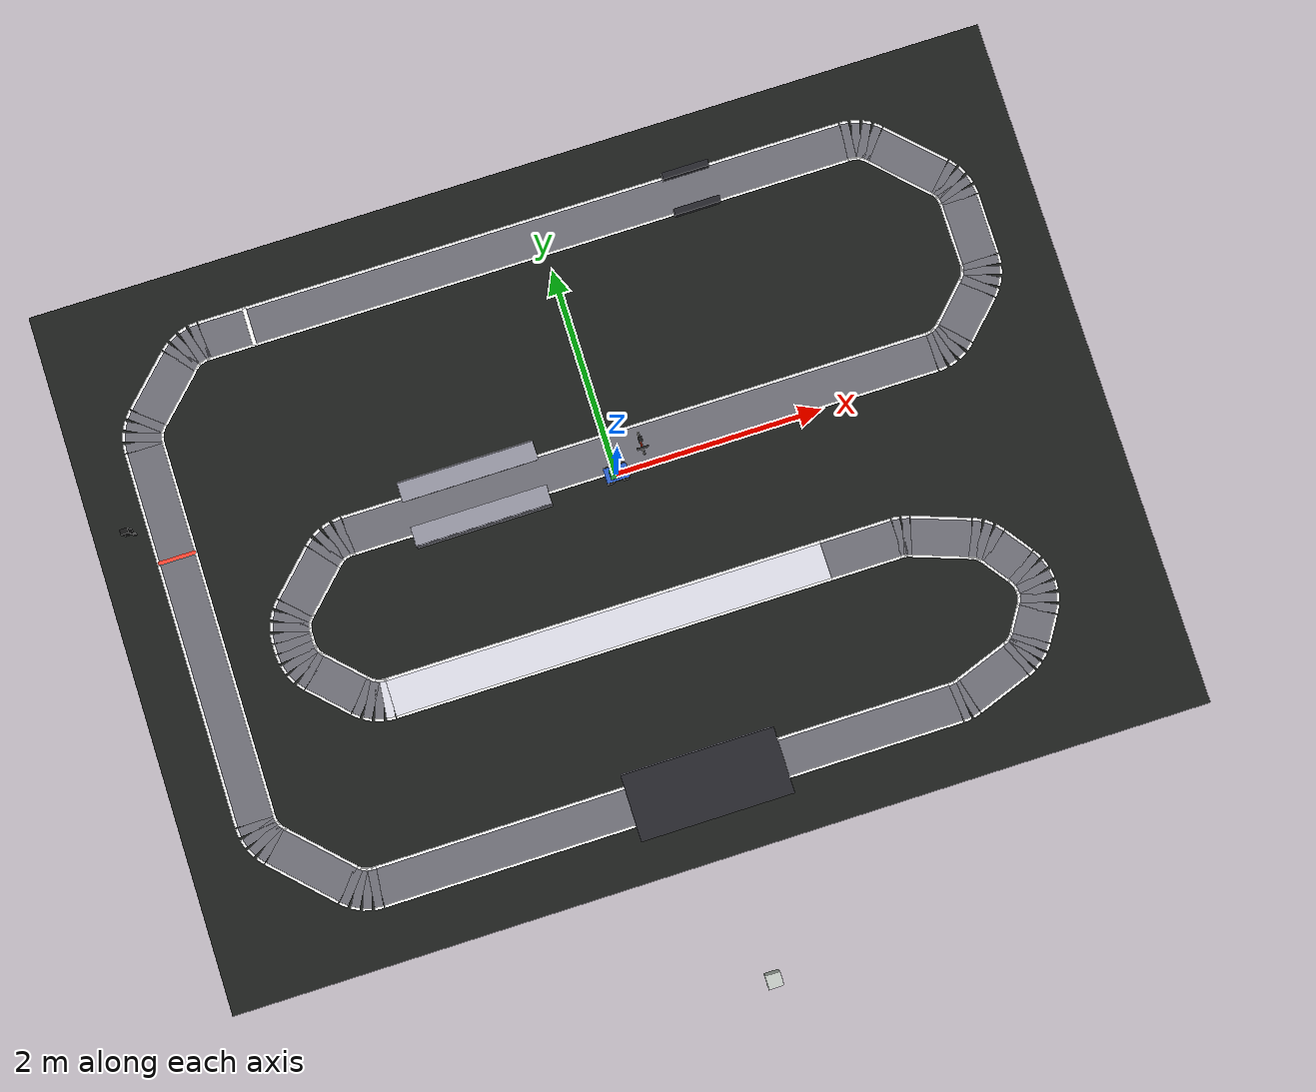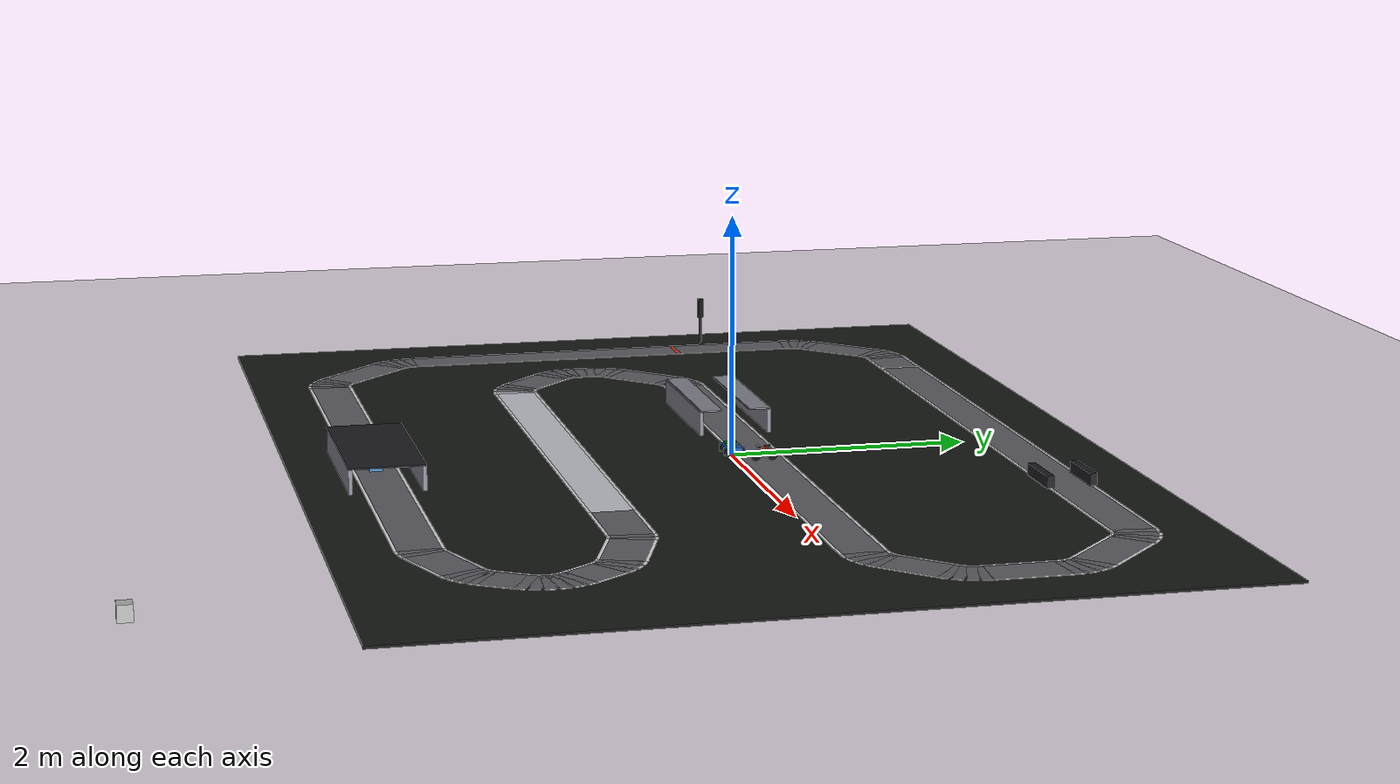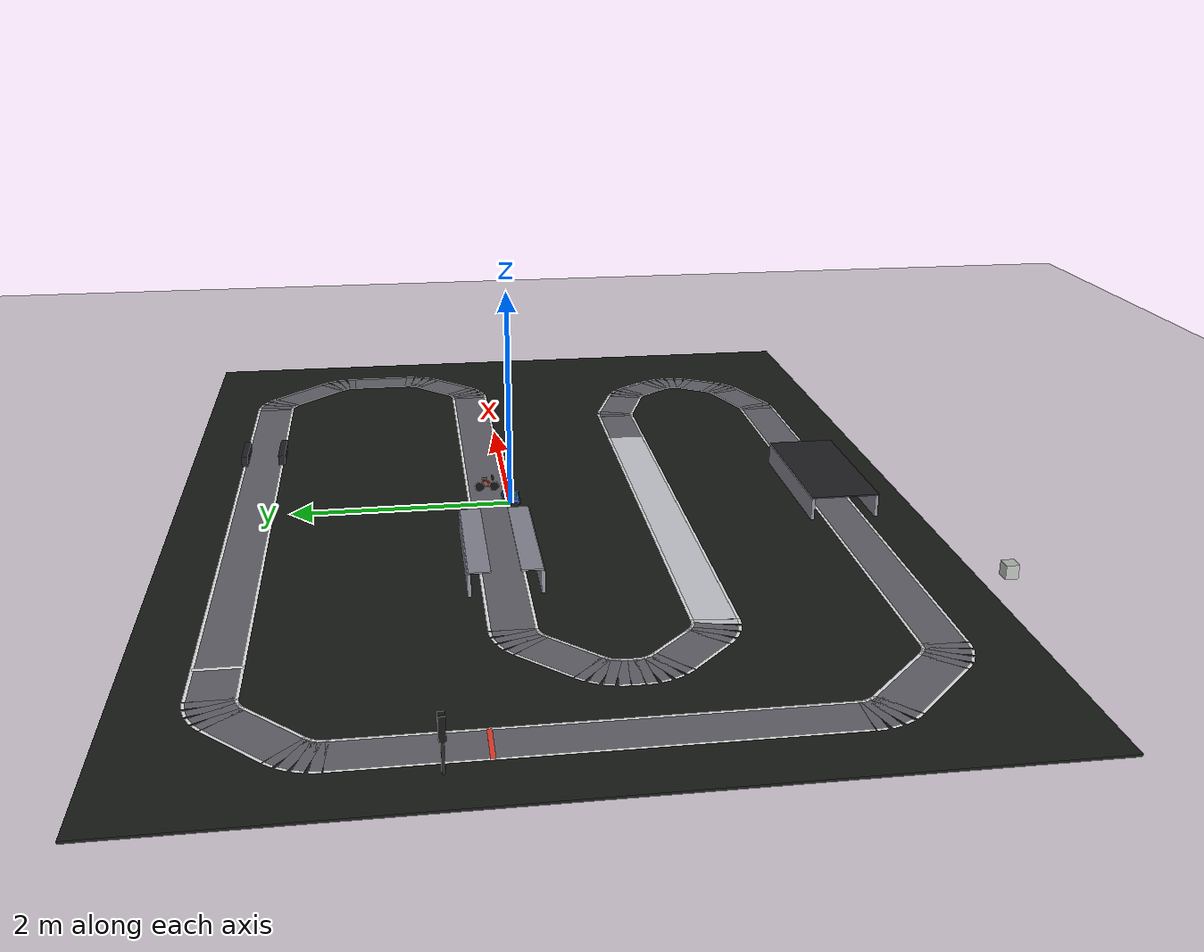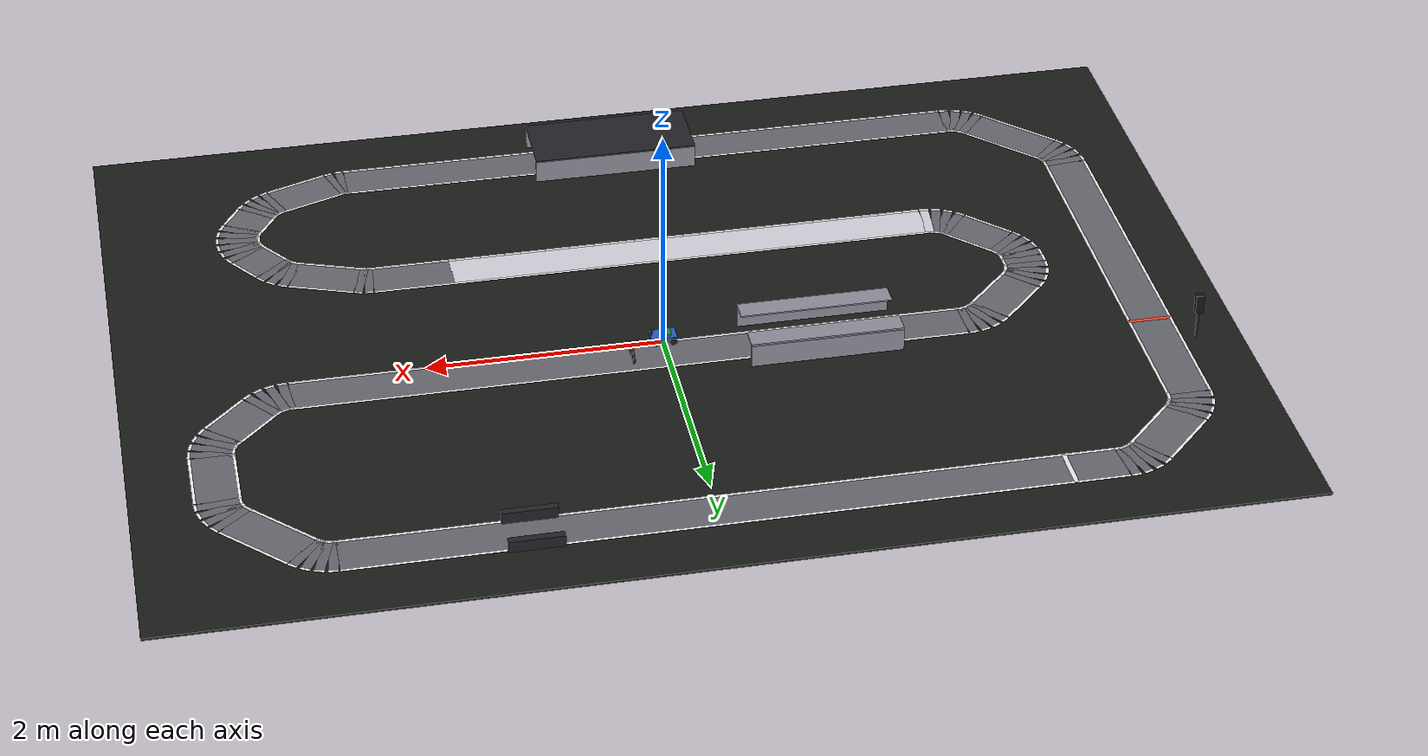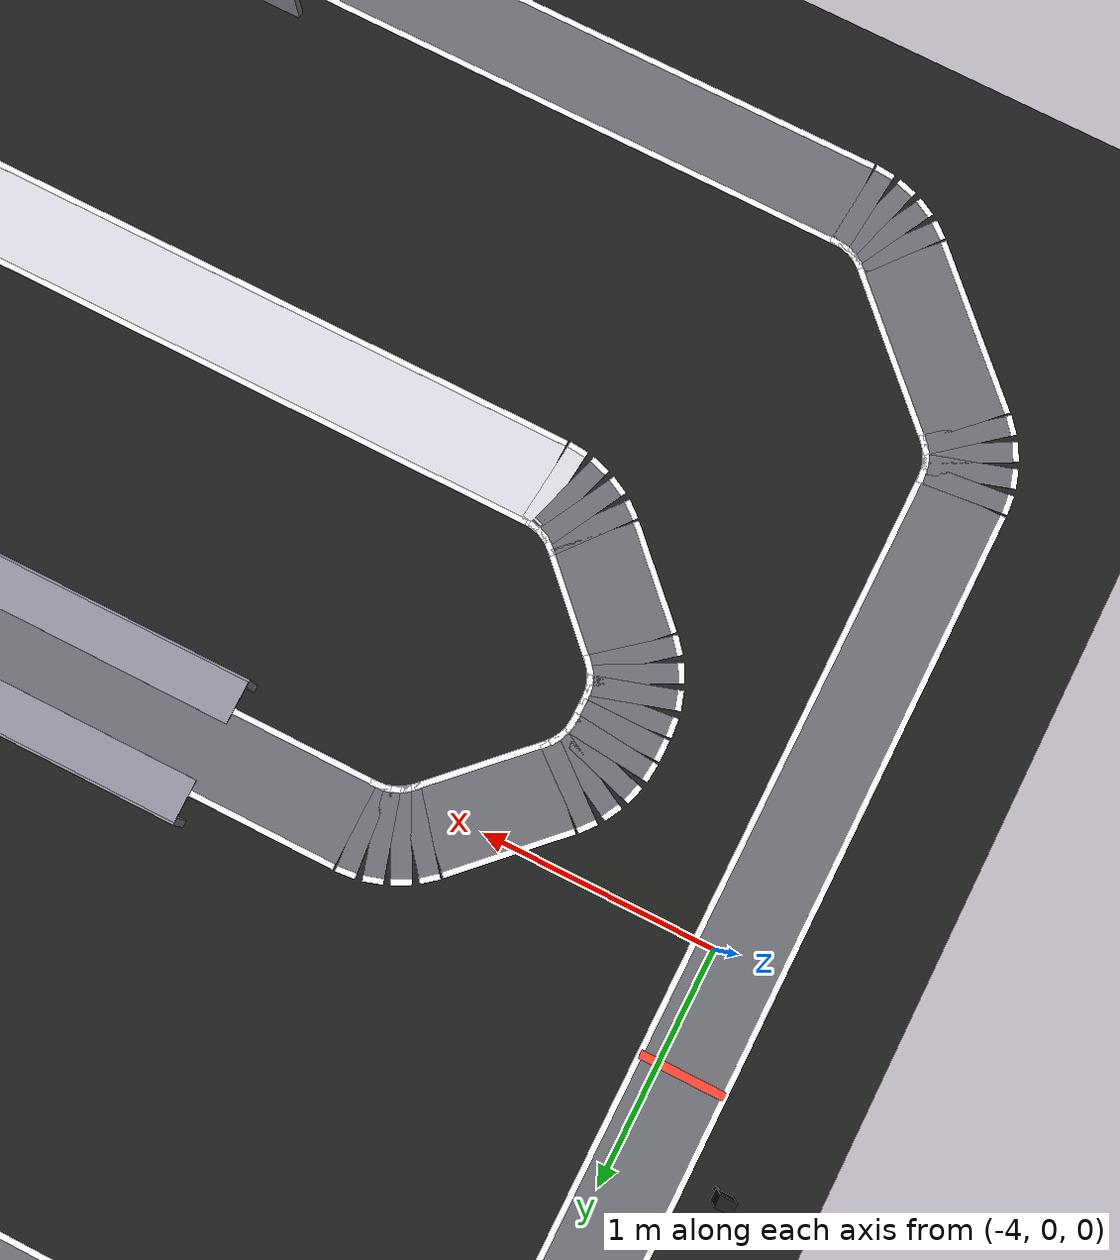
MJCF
<mujoco model="gauntlet">
  <compiler angle="radian" autolimits="true"/>
  <option timestep="0.002" integrator="implicitfast"/>

  <visual>
    <!-- offscreen framebuffer: must be >= the largest render requested.
         800x450 onboard camera; view_camera.py's chase panel is 600x450. -->
    <global offwidth="800" offheight="480"/>
    <!-- weak headlight so the tunnels are genuinely dark on camera -->
    <headlight diffuse="0.12 0.12 0.12" ambient="0.22 0.22 0.22"/>
  </visual>

  <asset>
    <texture type="skybox" builtin="gradient" rgb1="0.45 0.65 0.9" rgb2="0.9 0.95 1" width="256" height="256"/>
    <!-- dark ground surrounding the road, so the paved strip stands out -->
    <texture type="2d" name="carpet" builtin="checker" rgb1="0.09 0.10 0.09" rgb2="0.11 0.12 0.11"
             width="512" height="512"/>
    <material name="floor" texture="carpet" texrepeat="16 16" texuniform="true" reflectance="0" specular="0.1"/>
    <!-- paved road surface: mid gray, clearly brighter than the ground -->
    <material name="road" rgba="0.40 0.40 0.43 1" reflectance="0.05" specular="0.1"/>
    <material name="line" rgba="0.93 0.93 0.93 1"/>
    <!-- high-glare road: bright + strongly reflective, washes out edge contrast -->
    <material name="glare" rgba="0.82 0.82 0.86 1" reflectance="0.8" specular="1" shininess="1"/>
  </asset>

  <worldbody>
    <light directional="true" pos="3 -4 6" dir="-0.35 0.45 -0.85" diffuse="0.85 0.85 0.8" castshadow="true"/>
    <light name="tunnel1_light" pos="-1.30 0.20 0.21" dir="0 0 -1" diffuse="0.45 0.45 0.4" cutoff="70"/>

    <geom name="ground" type="plane" size="0 0 1" rgba="0.25 0.32 0.25 1"/>
    <geom name="floor" type="box" size="4.67 3.35 0.01"
          pos="-0.12 -0.30 0.01" material="floor"/>

    <geom name="road_0" type="box" size="3.1466 0.18 0.0006" pos="-0.1500 2.3500 0.0206" euler="0 0 0.0000" material="road" contype="0" conaffinity="0"/>
    <geom name="edge_0_l" type="box" size="3.1466 0.0125 0.0004" pos="-0.1500 2.5300 0.0212" euler="0 0 0.0000" material="line" contype="0" conaffinity="0"/>
    <geom name="edge_0_r" type="box" size="3.1466 0.0125 0.0004" pos="-0.1500 2.1700 0.0212" euler="0 0 0.0000" material="line" contype="0" conaffinity="0"/>
    <geom name="road_1" type="box" size="0.0413 0.18 0.0006" pos="3.0298 2.3482 0.0206" euler="0 0 -0.0982" material="road" contype="0" conaffinity="0"/>
    <geom name="edge_1_l" type="box" size="0.0413 0.0125 0.0004" pos="3.0475 2.5273 0.0212" euler="0 0 -0.0982" material="line" contype="0" conaffinity="0"/>
    <geom name="edge_1_r" type="box" size="0.0413 0.0125 0.0004" pos="3.0122 2.1690 0.0212" euler="0 0 -0.0982" material="line" contype="0" conaffinity="0"/>
    <geom name="road_2" type="box" size="0.0413 0.18 0.0006" pos="3.1029 2.3336 0.0206" euler="0 0 -0.2945" material="road" contype="0" conaffinity="0"/>
    <geom name="edge_2_l" type="box" size="0.0413 0.0125 0.0004" pos="3.1552 2.5059 0.0212" euler="0 0 -0.2945" material="line" contype="0" conaffinity="0"/>
    <geom name="edge_2_r" type="box" size="0.0413 0.0125 0.0004" pos="3.0507 2.1614 0.0212" euler="0 0 -0.2945" material="line" contype="0" conaffinity="0"/>
    <geom name="road_3" type="box" size="0.0413 0.18 0.0006" pos="3.1717 2.3051 0.0206" euler="0 0 -0.4909" material="road" contype="0" conaffinity="0"/>
    <geom name="edge_3_l" type="box" size="0.0413 0.0125 0.0004" pos="3.2566 2.4639 0.0212" euler="0 0 -0.4909" material="line" contype="0" conaffinity="0"/>
    <geom name="edge_3_r" type="box" size="0.0413 0.0125 0.0004" pos="3.0869 2.1464 0.0212" euler="0 0 -0.4909" material="line" contype="0" conaffinity="0"/>
    <geom name="road_4" type="box" size="0.0413 0.18 0.0006" pos="3.2337 2.2637 0.0206" euler="0 0 -0.6872" material="road" contype="0" conaffinity="0"/>
    <geom name="edge_4_l" type="box" size="0.0413 0.0125 0.0004" pos="3.3479 2.4029 0.0212" euler="0 0 -0.6872" material="line" contype="0" conaffinity="0"/>
    <geom name="edge_4_r" type="box" size="0.0413 0.0125 0.0004" pos="3.1195 2.1246 0.0212" euler="0 0 -0.6872" material="line" contype="0" conaffinity="0"/>
    <geom name="road_5" type="box" size="0.3416 0.18 0.0006" pos="3.5000 2.0000 0.0206" euler="0 0 -0.7854" material="road" contype="0" conaffinity="0"/>
    <geom name="edge_5_l" type="box" size="0.3416 0.0125 0.0004" pos="3.6273 2.1273 0.0212" euler="0 0 -0.7854" material="line" contype="0" conaffinity="0"/>
    <geom name="edge_5_r" type="box" size="0.3416 0.0125 0.0004" pos="3.3727 1.8727 0.0212" euler="0 0 -0.7854" material="line" contype="0" conaffinity="0"/>
    <geom name="road_6" type="box" size="0.0413 0.18 0.0006" pos="3.7637 1.7337 0.0206" euler="0 0 -0.8836" material="road" contype="0" conaffinity="0"/>
    <geom name="edge_6_l" type="box" size="0.0413 0.0125 0.0004" pos="3.9029 1.8479 0.0212" euler="0 0 -0.8836" material="line" contype="0" conaffinity="0"/>
    <geom name="edge_6_r" type="box" size="0.0413 0.0125 0.0004" pos="3.6246 1.6195 0.0212" euler="0 0 -0.8836" material="line" contype="0" conaffinity="0"/>
    <geom name="road_7" type="box" size="0.0413 0.18 0.0006" pos="3.8051 1.6717 0.0206" euler="0 0 -1.0799" material="road" contype="0" conaffinity="0"/>
    <geom name="edge_7_l" type="box" size="0.0413 0.0125 0.0004" pos="3.9639 1.7566 0.0212" euler="0 0 -1.0799" material="line" contype="0" conaffinity="0"/>
    <geom name="edge_7_r" type="box" size="0.0413 0.0125 0.0004" pos="3.6464 1.5869 0.0212" euler="0 0 -1.0799" material="line" contype="0" conaffinity="0"/>
    <geom name="road_8" type="box" size="0.0413 0.18 0.0006" pos="3.8336 1.6029 0.0206" euler="0 0 -1.2763" material="road" contype="0" conaffinity="0"/>
    <geom name="edge_8_l" type="box" size="0.0413 0.0125 0.0004" pos="4.0059 1.6552 0.0212" euler="0 0 -1.2763" material="line" contype="0" conaffinity="0"/>
    <geom name="edge_8_r" type="box" size="0.0413 0.0125 0.0004" pos="3.6614 1.5507 0.0212" euler="0 0 -1.2763" material="line" contype="0" conaffinity="0"/>
    <geom name="road_9" type="box" size="0.0413 0.18 0.0006" pos="3.8482 1.5298 0.0206" euler="0 0 -1.4726" material="road" contype="0" conaffinity="0"/>
    <geom name="edge_9_l" type="box" size="0.0413 0.0125 0.0004" pos="4.0273 1.5475 0.0212" euler="0 0 -1.4726" material="line" contype="0" conaffinity="0"/>
    <geom name="edge_9_r" type="box" size="0.0413 0.0125 0.0004" pos="3.6690 1.5122 0.0212" euler="0 0 -1.4726" material="line" contype="0" conaffinity="0"/>
    <geom name="road_10" type="box" size="0.2966 0.18 0.0006" pos="3.8500 1.2000 0.0206" euler="0 0 -1.5708" material="road" contype="0" conaffinity="0"/>
    <geom name="edge_10_l" type="box" size="0.2966 0.0125 0.0004" pos="4.0300 1.2000 0.0212" euler="0 0 -1.5708" material="line" contype="0" conaffinity="0"/>
    <geom name="edge_10_r" type="box" size="0.2966 0.0125 0.0004" pos="3.6700 1.2000 0.0212" euler="0 0 -1.5708" material="line" contype="0" conaffinity="0"/>
    <geom name="road_11" type="box" size="0.0413 0.18 0.0006" pos="3.8482 0.8702 0.0206" euler="0 0 -1.6690" material="road" contype="0" conaffinity="0"/>
    <geom name="edge_11_l" type="box" size="0.0413 0.0125 0.0004" pos="4.0273 0.8525 0.0212" euler="0 0 -1.6690" material="line" contype="0" conaffinity="0"/>
    <geom name="edge_11_r" type="box" size="0.0413 0.0125 0.0004" pos="3.6690 0.8878 0.0212" euler="0 0 -1.6690" material="line" contype="0" conaffinity="0"/>
    <geom name="road_12" type="box" size="0.0413 0.18 0.0006" pos="3.8336 0.7971 0.0206" euler="0 0 -1.8653" material="road" contype="0" conaffinity="0"/>
    <geom name="edge_12_l" type="box" size="0.0413 0.0125 0.0004" pos="4.0059 0.7448 0.0212" euler="0 0 -1.8653" material="line" contype="0" conaffinity="0"/>
    <geom name="edge_12_r" type="box" size="0.0413 0.0125 0.0004" pos="3.6614 0.8493 0.0212" euler="0 0 -1.8653" material="line" contype="0" conaffinity="0"/>
    <geom name="road_13" type="box" size="0.0413 0.18 0.0006" pos="3.8051 0.7283 0.0206" euler="0 0 -2.0617" material="road" contype="0" conaffinity="0"/>
    <geom name="edge_13_l" type="box" size="0.0413 0.0125 0.0004" pos="3.9639 0.6434 0.0212" euler="0 0 -2.0617" material="line" contype="0" conaffinity="0"/>
    <geom name="edge_13_r" type="box" size="0.0413 0.0125 0.0004" pos="3.6464 0.8131 0.0212" euler="0 0 -2.0617" material="line" contype="0" conaffinity="0"/>
    <geom name="road_14" type="box" size="0.0413 0.18 0.0006" pos="3.7637 0.6663 0.0206" euler="0 0 -2.2580" material="road" contype="0" conaffinity="0"/>
    <geom name="edge_14_l" type="box" size="0.0413 0.0125 0.0004" pos="3.9029 0.5521 0.0212" euler="0 0 -2.2580" material="line" contype="0" conaffinity="0"/>
    <geom name="edge_14_r" type="box" size="0.0413 0.0125 0.0004" pos="3.6246 0.7805 0.0212" euler="0 0 -2.2580" material="line" contype="0" conaffinity="0"/>
    <geom name="road_15" type="box" size="0.2355 0.18 0.0006" pos="3.5750 0.4750 0.0206" euler="0 0 -2.3562" material="road" contype="0" conaffinity="0"/>
    <geom name="edge_15_l" type="box" size="0.2355 0.0125 0.0004" pos="3.7023 0.3477 0.0212" euler="0 0 -2.3562" material="line" contype="0" conaffinity="0"/>
    <geom name="edge_15_r" type="box" size="0.2355 0.0125 0.0004" pos="3.4477 0.6023 0.0212" euler="0 0 -2.3562" material="line" contype="0" conaffinity="0"/>
    <geom name="road_16" type="box" size="0.0413 0.18 0.0006" pos="3.3837 0.2863 0.0206" euler="0 0 -2.4544" material="road" contype="0" conaffinity="0"/>
    <geom name="edge_16_l" type="box" size="0.0413 0.0125 0.0004" pos="3.4979 0.1471 0.0212" euler="0 0 -2.4544" material="line" contype="0" conaffinity="0"/>
    <geom name="edge_16_r" type="box" size="0.0413 0.0125 0.0004" pos="3.2695 0.4254 0.0212" euler="0 0 -2.4544" material="line" contype="0" conaffinity="0"/>
    <geom name="road_17" type="box" size="0.0413 0.18 0.0006" pos="3.3217 0.2449 0.0206" euler="0 0 -2.6507" material="road" contype="0" conaffinity="0"/>
    <geom name="edge_17_l" type="box" size="0.0413 0.0125 0.0004" pos="3.4066 0.0861 0.0212" euler="0 0 -2.6507" material="line" contype="0" conaffinity="0"/>
    <geom name="edge_17_r" type="box" size="0.0413 0.0125 0.0004" pos="3.2369 0.4036 0.0212" euler="0 0 -2.6507" material="line" contype="0" conaffinity="0"/>
    <geom name="road_18" type="box" size="0.0413 0.18 0.0006" pos="3.2529 0.2164 0.0206" euler="0 0 -2.8471" material="road" contype="0" conaffinity="0"/>
    <geom name="edge_18_l" type="box" size="0.0413 0.0125 0.0004" pos="3.3052 0.0441 0.0212" euler="0 0 -2.8471" material="line" contype="0" conaffinity="0"/>
    <geom name="edge_18_r" type="box" size="0.0413 0.0125 0.0004" pos="3.2007 0.3886 0.0212" euler="0 0 -2.8471" material="line" contype="0" conaffinity="0"/>
    <geom name="road_19" type="box" size="0.0413 0.18 0.0006" pos="3.1798 0.2018 0.0206" euler="0 0 -3.0434" material="road" contype="0" conaffinity="0"/>
    <geom name="edge_19_l" type="box" size="0.0413 0.0125 0.0004" pos="3.1975 0.0227 0.0212" euler="0 0 -3.0434" material="line" contype="0" conaffinity="0"/>
    <geom name="edge_19_r" type="box" size="0.0413 0.0125 0.0004" pos="3.1622 0.3810 0.0212" euler="0 0 -3.0434" material="line" contype="0" conaffinity="0"/>
    <geom name="road_20" type="box" size="2.8466 0.18 0.0006" pos="0.3000 0.2000 0.0206" euler="0 0 3.1416" material="road" contype="0" conaffinity="0"/>
    <geom name="edge_20_l" type="box" size="2.8466 0.0125 0.0004" pos="0.3000 0.0200 0.0212" euler="0 0 3.1416" material="line" contype="0" conaffinity="0"/>
    <geom name="edge_20_r" type="box" size="2.8466 0.0125 0.0004" pos="0.3000 0.3800 0.0212" euler="0 0 3.1416" material="line" contype="0" conaffinity="0"/>
    <geom name="road_21" type="box" size="0.0413 0.18 0.0006" pos="-2.5798 0.1982 0.0206" euler="0 0 3.2398" material="road" contype="0" conaffinity="0"/>
    <geom name="edge_21_l" type="box" size="0.0413 0.0125 0.0004" pos="-2.5622 0.0190 0.0212" euler="0 0 3.2398" material="line" contype="0" conaffinity="0"/>
    <geom name="edge_21_r" type="box" size="0.0413 0.0125 0.0004" pos="-2.5975 0.3773 0.0212" euler="0 0 3.2398" material="line" contype="0" conaffinity="0"/>
    <geom name="road_22" type="box" size="0.0413 0.18 0.0006" pos="-2.6529 0.1836 0.0206" euler="0 0 3.4361" material="road" contype="0" conaffinity="0"/>
    <geom name="edge_22_l" type="box" size="0.0413 0.0125 0.0004" pos="-2.6007 0.0114 0.0212" euler="0 0 3.4361" material="line" contype="0" conaffinity="0"/>
    <geom name="edge_22_r" type="box" size="0.0413 0.0125 0.0004" pos="-2.7052 0.3559 0.0212" euler="0 0 3.4361" material="line" contype="0" conaffinity="0"/>
    <geom name="road_23" type="box" size="0.0413 0.18 0.0006" pos="-2.7217 0.1551 0.0206" euler="0 0 3.6325" material="road" contype="0" conaffinity="0"/>
    <geom name="edge_23_l" type="box" size="0.0413 0.0125 0.0004" pos="-2.6369 -0.0036 0.0212" euler="0 0 3.6325" material="line" contype="0" conaffinity="0"/>
    <geom name="edge_23_r" type="box" size="0.0413 0.0125 0.0004" pos="-2.8066 0.3139 0.0212" euler="0 0 3.6325" material="line" contype="0" conaffinity="0"/>
    <geom name="road_24" type="box" size="0.0413 0.18 0.0006" pos="-2.7837 0.1137 0.0206" euler="0 0 3.8288" material="road" contype="0" conaffinity="0"/>
    <geom name="edge_24_l" type="box" size="0.0413 0.0125 0.0004" pos="-2.6695 -0.0254 0.0212" euler="0 0 3.8288" material="line" contype="0" conaffinity="0"/>
    <geom name="edge_24_r" type="box" size="0.0413 0.0125 0.0004" pos="-2.8979 0.2529 0.0212" euler="0 0 3.8288" material="line" contype="0" conaffinity="0"/>
    <geom name="road_25" type="box" size="0.2709 0.18 0.0006" pos="-3.0000 -0.1000 0.0206" euler="0 0 -2.3562" material="road" contype="0" conaffinity="0"/>
    <geom name="edge_25_l" type="box" size="0.2709 0.0125 0.0004" pos="-2.8727 -0.2273 0.0212" euler="0 0 -2.3562" material="line" contype="0" conaffinity="0"/>
    <geom name="edge_25_r" type="box" size="0.2709 0.0125 0.0004" pos="-3.1273 0.0273 0.0212" euler="0 0 -2.3562" material="line" contype="0" conaffinity="0"/>
    <geom name="road_26" type="box" size="0.0413 0.18 0.0006" pos="-3.2137 -0.3163 0.0206" euler="0 0 4.0252" material="road" contype="0" conaffinity="0"/>
    <geom name="edge_26_l" type="box" size="0.0413 0.0125 0.0004" pos="-3.0746 -0.4305 0.0212" euler="0 0 4.0252" material="line" contype="0" conaffinity="0"/>
    <geom name="edge_26_r" type="box" size="0.0413 0.0125 0.0004" pos="-3.3529 -0.2021 0.0212" euler="0 0 4.0252" material="line" contype="0" conaffinity="0"/>
    <geom name="road_27" type="box" size="0.0413 0.18 0.0006" pos="-3.2551 -0.3783 0.0206" euler="0 0 4.2215" material="road" contype="0" conaffinity="0"/>
    <geom name="edge_27_l" type="box" size="0.0413 0.0125 0.0004" pos="-3.0964 -0.4631 0.0212" euler="0 0 4.2215" material="line" contype="0" conaffinity="0"/>
    <geom name="edge_27_r" type="box" size="0.0413 0.0125 0.0004" pos="-3.4139 -0.2934 0.0212" euler="0 0 4.2215" material="line" contype="0" conaffinity="0"/>
    <geom name="road_28" type="box" size="0.0413 0.18 0.0006" pos="-3.2836 -0.4471 0.0206" euler="0 0 4.4179" material="road" contype="0" conaffinity="0"/>
    <geom name="edge_28_l" type="box" size="0.0413 0.0125 0.0004" pos="-3.1114 -0.4993 0.0212" euler="0 0 4.4179" material="line" contype="0" conaffinity="0"/>
    <geom name="edge_28_r" type="box" size="0.0413 0.0125 0.0004" pos="-3.4559 -0.3948 0.0212" euler="0 0 4.4179" material="line" contype="0" conaffinity="0"/>
    <geom name="road_29" type="box" size="0.0413 0.18 0.0006" pos="-3.2982 -0.5202 0.0206" euler="0 0 4.6142" material="road" contype="0" conaffinity="0"/>
    <geom name="edge_29_l" type="box" size="0.0413 0.0125 0.0004" pos="-3.1190 -0.5378 0.0212" euler="0 0 4.6142" material="line" contype="0" conaffinity="0"/>
    <geom name="edge_29_r" type="box" size="0.0413 0.0125 0.0004" pos="-3.4773 -0.5025 0.0212" euler="0 0 4.6142" material="line" contype="0" conaffinity="0"/>
    <geom name="road_30" type="box" size="0.0466 0.18 0.0006" pos="-3.3000 -0.6000 0.0206" euler="0 0 -1.5708" material="road" contype="0" conaffinity="0"/>
    <geom name="edge_30_l" type="box" size="0.0466 0.0125 0.0004" pos="-3.1200 -0.6000 0.0212" euler="0 0 -1.5708" material="line" contype="0" conaffinity="0"/>
    <geom name="edge_30_r" type="box" size="0.0466 0.0125 0.0004" pos="-3.4800 -0.6000 0.0212" euler="0 0 -1.5708" material="line" contype="0" conaffinity="0"/>
    <geom name="road_31" type="box" size="0.0413 0.18 0.0006" pos="-3.2982 -0.6798 0.0206" euler="0 0 4.8106" material="road" contype="0" conaffinity="0"/>
    <geom name="edge_31_l" type="box" size="0.0413 0.0125 0.0004" pos="-3.1190 -0.6622 0.0212" euler="0 0 4.8106" material="line" contype="0" conaffinity="0"/>
    <geom name="edge_31_r" type="box" size="0.0413 0.0125 0.0004" pos="-3.4773 -0.6975 0.0212" euler="0 0 4.8106" material="line" contype="0" conaffinity="0"/>
    <geom name="road_32" type="box" size="0.0413 0.18 0.0006" pos="-3.2836 -0.7529 0.0206" euler="0 0 5.0069" material="road" contype="0" conaffinity="0"/>
    <geom name="edge_32_l" type="box" size="0.0413 0.0125 0.0004" pos="-3.1114 -0.7007 0.0212" euler="0 0 5.0069" material="line" contype="0" conaffinity="0"/>
    <geom name="edge_32_r" type="box" size="0.0413 0.0125 0.0004" pos="-3.4559 -0.8052 0.0212" euler="0 0 5.0069" material="line" contype="0" conaffinity="0"/>
    <geom name="road_33" type="box" size="0.0413 0.18 0.0006" pos="-3.2551 -0.8217 0.0206" euler="0 0 5.2033" material="road" contype="0" conaffinity="0"/>
    <geom name="edge_33_l" type="box" size="0.0413 0.0125 0.0004" pos="-3.0964 -0.7369 0.0212" euler="0 0 5.2033" material="line" contype="0" conaffinity="0"/>
    <geom name="edge_33_r" type="box" size="0.0413 0.0125 0.0004" pos="-3.4139 -0.9066 0.0212" euler="0 0 5.2033" material="line" contype="0" conaffinity="0"/>
    <geom name="road_34" type="box" size="0.0413 0.18 0.0006" pos="-3.2137 -0.8837 0.0206" euler="0 0 5.3996" material="road" contype="0" conaffinity="0"/>
    <geom name="edge_34_l" type="box" size="0.0413 0.0125 0.0004" pos="-3.0746 -0.7695 0.0212" euler="0 0 5.3996" material="line" contype="0" conaffinity="0"/>
    <geom name="edge_34_r" type="box" size="0.0413 0.0125 0.0004" pos="-3.3529 -0.9979 0.0212" euler="0 0 5.3996" material="line" contype="0" conaffinity="0"/>
    <geom name="road_35" type="box" size="0.2355 0.18 0.0006" pos="-3.0250 -1.0750 0.0206" euler="0 0 -0.7854" material="road" contype="0" conaffinity="0"/>
    <geom name="edge_35_l" type="box" size="0.2355 0.0125 0.0004" pos="-2.8977 -0.9477 0.0212" euler="0 0 -0.7854" material="line" contype="0" conaffinity="0"/>
    <geom name="edge_35_r" type="box" size="0.2355 0.0125 0.0004" pos="-3.1523 -1.2023 0.0212" euler="0 0 -0.7854" material="line" contype="0" conaffinity="0"/>
    <geom name="road_36" type="box" size="0.0413 0.18 0.0006" pos="-2.8337 -1.2637 0.0206" euler="0 0 -0.6872" material="road" contype="0" conaffinity="0"/>
    <geom name="edge_36_l" type="box" size="0.0413 0.0125 0.0004" pos="-2.7195 -1.1246 0.0212" euler="0 0 -0.6872" material="line" contype="0" conaffinity="0"/>
    <geom name="edge_36_r" type="box" size="0.0413 0.0125 0.0004" pos="-2.9479 -1.4029 0.0212" euler="0 0 -0.6872" material="line" contype="0" conaffinity="0"/>
    <geom name="road_37" type="box" size="0.0413 0.18 0.0006" pos="-2.7717 -1.3051 0.0206" euler="0 0 -0.4909" material="road" contype="0" conaffinity="0"/>
    <geom name="edge_37_l" type="box" size="0.0413 0.0125 0.0004" pos="-2.6869 -1.1464 0.0212" euler="0 0 -0.4909" material="line" contype="0" conaffinity="0"/>
    <geom name="edge_37_r" type="box" size="0.0413 0.0125 0.0004" pos="-2.8566 -1.4639 0.0212" euler="0 0 -0.4909" material="line" contype="0" conaffinity="0"/>
    <geom name="road_38" type="box" size="0.0413 0.18 0.0006" pos="-2.7029 -1.3336 0.0206" euler="0 0 -0.2945" material="road" contype="0" conaffinity="0"/>
    <geom name="edge_38_l" type="box" size="0.0413 0.0125 0.0004" pos="-2.6507 -1.1614 0.0212" euler="0 0 -0.2945" material="line" contype="0" conaffinity="0"/>
    <geom name="edge_38_r" type="box" size="0.0413 0.0125 0.0004" pos="-2.7552 -1.5059 0.0212" euler="0 0 -0.2945" material="line" contype="0" conaffinity="0"/>
    <geom name="road_39" type="box" size="0.0413 0.18 0.0006" pos="-2.6298 -1.3482 0.0206" euler="0 0 -0.0982" material="glare" contype="0" conaffinity="0"/>
    <geom name="edge_39_l" type="box" size="0.0413 0.0125 0.0004" pos="-2.6122 -1.1690 0.0212" euler="0 0 -0.0982" material="line" contype="0" conaffinity="0"/>
    <geom name="edge_39_r" type="box" size="0.0413 0.0125 0.0004" pos="-2.6475 -1.5273 0.0212" euler="0 0 -0.0982" material="line" contype="0" conaffinity="0"/>
    <geom name="road_40" type="box" size="2.1003 0.18 0.0006" pos="-0.4963 -1.3500 0.0206" euler="0 0 0.0000" material="glare" contype="0" conaffinity="0"/>
    <geom name="edge_40_l" type="box" size="2.1003 0.0125 0.0004" pos="-0.4963 -1.1700 0.0212" euler="0 0 0.0000" material="line" contype="0" conaffinity="0"/>
    <geom name="edge_40_r" type="box" size="2.1003 0.0125 0.0004" pos="-0.4963 -1.5300 0.0212" euler="0 0 0.0000" material="line" contype="0" conaffinity="0"/>
    <geom name="road_41" type="box" size="0.3461 0.18 0.0006" pos="1.9421 -1.3500 0.0206" euler="0 0 0.0000" material="road" contype="0" conaffinity="0"/>
    <geom name="edge_41_l" type="box" size="0.3461 0.0125 0.0004" pos="1.9421 -1.1700 0.0212" euler="0 0 0.0000" material="line" contype="0" conaffinity="0"/>
    <geom name="edge_41_r" type="box" size="0.3461 0.0125 0.0004" pos="1.9421 -1.5300 0.0212" euler="0 0 0.0000" material="line" contype="0" conaffinity="0"/>
    <geom name="road_42" type="box" size="0.0366 0.18 0.0006" pos="2.3167 -1.3514 0.0206" euler="0 0 -0.0858" material="road" contype="0" conaffinity="0"/>
    <geom name="edge_42_l" type="box" size="0.0366 0.0125 0.0004" pos="2.3321 -1.1721 0.0212" euler="0 0 -0.0858" material="line" contype="0" conaffinity="0"/>
    <geom name="edge_42_r" type="box" size="0.0366 0.0125 0.0004" pos="2.3013 -1.5307 0.0212" euler="0 0 -0.0858" material="line" contype="0" conaffinity="0"/>
    <geom name="road_43" type="box" size="0.0366 0.18 0.0006" pos="2.3809 -1.3625 0.0206" euler="0 0 -0.2573" material="road" contype="0" conaffinity="0"/>
    <geom name="edge_43_l" type="box" size="0.0366 0.0125 0.0004" pos="2.4267 -1.1884 0.0212" euler="0 0 -0.2573" material="line" contype="0" conaffinity="0"/>
    <geom name="edge_43_r" type="box" size="0.0366 0.0125 0.0004" pos="2.3351 -1.5366 0.0212" euler="0 0 -0.2573" material="line" contype="0" conaffinity="0"/>
    <geom name="road_44" type="box" size="0.2841 0.18 0.0006" pos="2.6757 -1.4663 0.0206" euler="0 0 -0.3430" material="road" contype="0" conaffinity="0"/>
    <geom name="edge_44_l" type="box" size="0.2841 0.0125 0.0004" pos="2.7363 -1.2968 0.0212" euler="0 0 -0.3430" material="line" contype="0" conaffinity="0"/>
    <geom name="edge_44_r" type="box" size="0.2841 0.0125 0.0004" pos="2.6152 -1.6359 0.0212" euler="0 0 -0.3430" material="line" contype="0" conaffinity="0"/>
    <geom name="road_45" type="box" size="0.0419 0.18 0.0006" pos="2.9745 -1.5751 0.0206" euler="0 0 -0.4429" material="road" contype="0" conaffinity="0"/>
    <geom name="edge_45_l" type="box" size="0.0419 0.0125 0.0004" pos="3.0517 -1.4124 0.0212" euler="0 0 -0.4429" material="line" contype="0" conaffinity="0"/>
    <geom name="edge_45_r" type="box" size="0.0419 0.0125 0.0004" pos="2.8974 -1.7377 0.0212" euler="0 0 -0.4429" material="line" contype="0" conaffinity="0"/>
    <geom name="road_46" type="box" size="0.0419 0.18 0.0006" pos="3.0394 -1.6142 0.0206" euler="0 0 -0.6425" material="road" contype="0" conaffinity="0"/>
    <geom name="edge_46_l" type="box" size="0.0419 0.0125 0.0004" pos="3.1472 -1.4701 0.0212" euler="0 0 -0.6425" material="line" contype="0" conaffinity="0"/>
    <geom name="edge_46_r" type="box" size="0.0419 0.0125 0.0004" pos="2.9315 -1.7583 0.0212" euler="0 0 -0.6425" material="line" contype="0" conaffinity="0"/>
    <geom name="road_47" type="box" size="0.0419 0.18 0.0006" pos="3.0952 -1.6654 0.0206" euler="0 0 -0.8422" material="road" contype="0" conaffinity="0"/>
    <geom name="edge_47_l" type="box" size="0.0419 0.0125 0.0004" pos="3.2295 -1.5455 0.0212" euler="0 0 -0.8422" material="line" contype="0" conaffinity="0"/>
    <geom name="edge_47_r" type="box" size="0.0419 0.0125 0.0004" pos="2.9609 -1.7852 0.0212" euler="0 0 -0.8422" material="line" contype="0" conaffinity="0"/>
    <geom name="road_48" type="box" size="0.1560 0.18 0.0006" pos="3.2084 -1.8178 0.0206" euler="0 0 -0.9420" material="road" contype="0" conaffinity="0"/>
    <geom name="edge_48_l" type="box" size="0.1560 0.0125 0.0004" pos="3.3540 -1.7120 0.0212" euler="0 0 -0.9420" material="line" contype="0" conaffinity="0"/>
    <geom name="edge_48_r" type="box" size="0.1560 0.0125 0.0004" pos="3.0628 -1.9237 0.0212" euler="0 0 -0.9420" material="line" contype="0" conaffinity="0"/>
    <geom name="road_49" type="box" size="0.0419 0.18 0.0006" pos="3.3185 -1.9724 0.0206" euler="0 0 -1.0416" material="road" contype="0" conaffinity="0"/>
    <geom name="edge_49_l" type="box" size="0.0419 0.0125 0.0004" pos="3.4739 -1.8816 0.0212" euler="0 0 -1.0416" material="line" contype="0" conaffinity="0"/>
    <geom name="edge_49_r" type="box" size="0.0419 0.0125 0.0004" pos="3.1632 -2.0633 0.0212" euler="0 0 -1.0416" material="line" contype="0" conaffinity="0"/>
    <geom name="road_50" type="box" size="0.0419 0.18 0.0006" pos="3.3500 -2.0412 0.0206" euler="0 0 -1.2409" material="road" contype="0" conaffinity="0"/>
    <geom name="edge_50_l" type="box" size="0.0419 0.0125 0.0004" pos="3.5203 -1.9828 0.0212" euler="0 0 -1.2409" material="line" contype="0" conaffinity="0"/>
    <geom name="edge_50_r" type="box" size="0.0419 0.0125 0.0004" pos="3.1797 -2.0995 0.0212" euler="0 0 -1.2409" material="line" contype="0" conaffinity="0"/>
    <geom name="road_51" type="box" size="0.0419 0.18 0.0006" pos="3.3673 -2.1148 0.0206" euler="0 0 -1.4401" material="road" contype="0" conaffinity="0"/>
    <geom name="edge_51_l" type="box" size="0.0419 0.0125 0.0004" pos="3.5457 -2.0913 0.0212" euler="0 0 -1.4401" material="line" contype="0" conaffinity="0"/>
    <geom name="edge_51_r" type="box" size="0.0419 0.0125 0.0004" pos="3.1888 -2.1382 0.0212" euler="0 0 -1.4401" material="line" contype="0" conaffinity="0"/>
    <geom name="road_52" type="box" size="0.0419 0.18 0.0006" pos="3.3696 -2.1903 0.0206" euler="0 0 -1.6394" material="road" contype="0" conaffinity="0"/>
    <geom name="edge_52_l" type="box" size="0.0419 0.0125 0.0004" pos="3.5492 -2.2026 0.0212" euler="0 0 -1.6394" material="line" contype="0" conaffinity="0"/>
    <geom name="edge_52_r" type="box" size="0.0419 0.0125 0.0004" pos="3.1900 -2.1780 0.0212" euler="0 0 -1.6394" material="line" contype="0" conaffinity="0"/>
    <geom name="road_53" type="box" size="0.0419 0.18 0.0006" pos="3.3570 -2.2648 0.0206" euler="0 0 -1.8386" material="road" contype="0" conaffinity="0"/>
    <geom name="edge_53_l" type="box" size="0.0419 0.0125 0.0004" pos="3.5305 -2.3125 0.0212" euler="0 0 -1.8386" material="line" contype="0" conaffinity="0"/>
    <geom name="edge_53_r" type="box" size="0.0419 0.0125 0.0004" pos="3.1834 -2.2172 0.0212" euler="0 0 -1.8386" material="line" contype="0" conaffinity="0"/>
    <geom name="road_54" type="box" size="0.0419 0.18 0.0006" pos="3.3298 -2.3354 0.0206" euler="0 0 -2.0379" material="road" contype="0" conaffinity="0"/>
    <geom name="edge_54_l" type="box" size="0.0419 0.0125 0.0004" pos="3.4905 -2.4164 0.0212" euler="0 0 -2.0379" material="line" contype="0" conaffinity="0"/>
    <geom name="edge_54_r" type="box" size="0.0419 0.0125 0.0004" pos="3.1691 -2.2543 0.0212" euler="0 0 -2.0379" material="line" contype="0" conaffinity="0"/>
    <geom name="road_55" type="box" size="0.1354 0.18 0.0006" pos="3.2405 -2.4791 0.0206" euler="0 0 -2.1375" material="road" contype="0" conaffinity="0"/>
    <geom name="edge_55_l" type="box" size="0.1354 0.0125 0.0004" pos="3.3924 -2.5758 0.0212" euler="0 0 -2.1375" material="line" contype="0" conaffinity="0"/>
    <geom name="edge_55_r" type="box" size="0.1354 0.0125 0.0004" pos="3.0887 -2.3825 0.0212" euler="0 0 -2.1375" material="line" contype="0" conaffinity="0"/>
    <geom name="road_56" type="box" size="0.0354 0.18 0.0006" pos="3.1521 -2.6158 0.0206" euler="0 0 -2.2202" material="road" contype="0" conaffinity="0"/>
    <geom name="edge_56_l" type="box" size="0.0354 0.0125 0.0004" pos="3.2954 -2.7246 0.0212" euler="0 0 -2.2202" material="line" contype="0" conaffinity="0"/>
    <geom name="edge_56_r" type="box" size="0.0354 0.0125 0.0004" pos="3.0087 -2.5069 0.0212" euler="0 0 -2.2202" material="line" contype="0" conaffinity="0"/>
    <geom name="road_57" type="box" size="0.0354 0.18 0.0006" pos="3.1101 -2.6624 0.0206" euler="0 0 -2.3854" material="road" contype="0" conaffinity="0"/>
    <geom name="edge_57_l" type="box" size="0.0354 0.0125 0.0004" pos="3.2336 -2.7934 0.0212" euler="0 0 -2.3854" material="line" contype="0" conaffinity="0"/>
    <geom name="edge_57_r" type="box" size="0.0354 0.0125 0.0004" pos="2.9866 -2.5315 0.0212" euler="0 0 -2.3854" material="line" contype="0" conaffinity="0"/>
    <geom name="road_58" type="box" size="0.0354 0.18 0.0006" pos="3.0611 -2.7016 0.0206" euler="0 0 -2.5507" material="road" contype="0" conaffinity="0"/>
    <geom name="edge_58_l" type="box" size="0.0354 0.0125 0.0004" pos="3.1614 -2.8510 0.0212" euler="0 0 -2.5507" material="line" contype="0" conaffinity="0"/>
    <geom name="edge_58_r" type="box" size="0.0354 0.0125 0.0004" pos="2.9608 -2.5521 0.0212" euler="0 0 -2.5507" material="line" contype="0" conaffinity="0"/>
    <geom name="road_59" type="box" size="0.0354 0.18 0.0006" pos="3.0063 -2.7321 0.0206" euler="0 0 -2.7159" material="road" contype="0" conaffinity="0"/>
    <geom name="edge_59_l" type="box" size="0.0354 0.0125 0.0004" pos="3.0806 -2.8960 0.0212" euler="0 0 -2.7159" material="line" contype="0" conaffinity="0"/>
    <geom name="edge_59_r" type="box" size="0.0354 0.0125 0.0004" pos="2.9320 -2.5681 0.0212" euler="0 0 -2.7159" material="line" contype="0" conaffinity="0"/>
    <geom name="road_60" type="box" size="0.2776 0.18 0.0006" pos="2.7196 -2.8359 0.0206" euler="0 0 -2.7986" material="road" contype="0" conaffinity="0"/>
    <geom name="edge_60_l" type="box" size="0.2776 0.0125 0.0004" pos="2.7801 -3.0054 0.0212" euler="0 0 -2.7986" material="line" contype="0" conaffinity="0"/>
    <geom name="edge_60_r" type="box" size="0.2776 0.0125 0.0004" pos="2.6591 -2.6663 0.0212" euler="0 0 -2.7986" material="line" contype="0" conaffinity="0"/>
    <geom name="road_61" type="box" size="0.0366 0.18 0.0006" pos="2.4309 -2.9375 0.0206" euler="0 0 -2.8843" material="road" contype="0" conaffinity="0"/>
    <geom name="edge_61_l" type="box" size="0.0366 0.0125 0.0004" pos="2.4767 -3.1116 0.0212" euler="0 0 -2.8843" material="line" contype="0" conaffinity="0"/>
    <geom name="edge_61_r" type="box" size="0.0366 0.0125 0.0004" pos="2.3851 -2.7634 0.0212" euler="0 0 -2.8843" material="line" contype="0" conaffinity="0"/>
    <geom name="road_62" type="box" size="0.0366 0.18 0.0006" pos="2.3667 -2.9486 0.0206" euler="0 0 -3.0558" material="road" contype="0" conaffinity="0"/>
    <geom name="edge_62_l" type="box" size="0.0366 0.0125 0.0004" pos="2.3821 -3.1279 0.0212" euler="0 0 -3.0558" material="line" contype="0" conaffinity="0"/>
    <geom name="edge_62_r" type="box" size="0.0366 0.0125 0.0004" pos="2.3513 -2.7693 0.0212" euler="0 0 -3.0558" material="line" contype="0" conaffinity="0"/>
    <geom name="road_63" type="box" size="2.7674 0.18 0.0006" pos="-0.4292 -2.9500 0.0206" euler="0 0 3.1416" material="road" contype="0" conaffinity="0"/>
    <geom name="edge_63_l" type="box" size="2.7674 0.0125 0.0004" pos="-0.4292 -3.1300 0.0212" euler="0 0 3.1416" material="line" contype="0" conaffinity="0"/>
    <geom name="edge_63_r" type="box" size="2.7674 0.0125 0.0004" pos="-0.4292 -2.7700 0.0212" euler="0 0 3.1416" material="line" contype="0" conaffinity="0"/>
    <geom name="road_64" type="box" size="0.0413 0.18 0.0006" pos="-3.2298 -2.9482 0.0206" euler="0 0 -3.2398" material="road" contype="0" conaffinity="0"/>
    <geom name="edge_64_l" type="box" size="0.0413 0.0125 0.0004" pos="-3.2475 -3.1273 0.0212" euler="0 0 -3.2398" material="line" contype="0" conaffinity="0"/>
    <geom name="edge_64_r" type="box" size="0.0413 0.0125 0.0004" pos="-3.2122 -2.7690 0.0212" euler="0 0 -3.2398" material="line" contype="0" conaffinity="0"/>
    <geom name="road_65" type="box" size="0.0413 0.18 0.0006" pos="-3.3029 -2.9336 0.0206" euler="0 0 -3.4361" material="road" contype="0" conaffinity="0"/>
    <geom name="edge_65_l" type="box" size="0.0413 0.0125 0.0004" pos="-3.3552 -3.1059 0.0212" euler="0 0 -3.4361" material="line" contype="0" conaffinity="0"/>
    <geom name="edge_65_r" type="box" size="0.0413 0.0125 0.0004" pos="-3.2507 -2.7614 0.0212" euler="0 0 -3.4361" material="line" contype="0" conaffinity="0"/>
    <geom name="road_66" type="box" size="0.0413 0.18 0.0006" pos="-3.3717 -2.9051 0.0206" euler="0 0 -3.6325" material="road" contype="0" conaffinity="0"/>
    <geom name="edge_66_l" type="box" size="0.0413 0.0125 0.0004" pos="-3.4566 -3.0639 0.0212" euler="0 0 -3.6325" material="line" contype="0" conaffinity="0"/>
    <geom name="edge_66_r" type="box" size="0.0413 0.0125 0.0004" pos="-3.2869 -2.7464 0.0212" euler="0 0 -3.6325" material="line" contype="0" conaffinity="0"/>
    <geom name="road_67" type="box" size="0.0413 0.18 0.0006" pos="-3.4337 -2.8637 0.0206" euler="0 0 -3.8288" material="road" contype="0" conaffinity="0"/>
    <geom name="edge_67_l" type="box" size="0.0413 0.0125 0.0004" pos="-3.5479 -3.0029 0.0212" euler="0 0 -3.8288" material="line" contype="0" conaffinity="0"/>
    <geom name="edge_67_r" type="box" size="0.0413 0.0125 0.0004" pos="-3.3195 -2.7246 0.0212" euler="0 0 -3.8288" material="line" contype="0" conaffinity="0"/>
    <geom name="road_68" type="box" size="0.3769 0.18 0.0006" pos="-3.7250 -2.5750 0.0206" euler="0 0 2.3562" material="road" contype="0" conaffinity="0"/>
    <geom name="edge_68_l" type="box" size="0.3769 0.0125 0.0004" pos="-3.8523 -2.7023 0.0212" euler="0 0 2.3562" material="line" contype="0" conaffinity="0"/>
    <geom name="edge_68_r" type="box" size="0.3769 0.0125 0.0004" pos="-3.5977 -2.4477 0.0212" euler="0 0 2.3562" material="line" contype="0" conaffinity="0"/>
    <geom name="road_69" type="box" size="0.0413 0.18 0.0006" pos="-4.0137 -2.2837 0.0206" euler="0 0 -4.0252" material="road" contype="0" conaffinity="0"/>
    <geom name="edge_69_l" type="box" size="0.0413 0.0125 0.0004" pos="-4.1529 -2.3979 0.0212" euler="0 0 -4.0252" material="line" contype="0" conaffinity="0"/>
    <geom name="edge_69_r" type="box" size="0.0413 0.0125 0.0004" pos="-3.8746 -2.1695 0.0212" euler="0 0 -4.0252" material="line" contype="0" conaffinity="0"/>
    <geom name="road_70" type="box" size="0.0413 0.18 0.0006" pos="-4.0551 -2.2217 0.0206" euler="0 0 -4.2215" material="road" contype="0" conaffinity="0"/>
    <geom name="edge_70_l" type="box" size="0.0413 0.0125 0.0004" pos="-4.2139 -2.3066 0.0212" euler="0 0 -4.2215" material="line" contype="0" conaffinity="0"/>
    <geom name="edge_70_r" type="box" size="0.0413 0.0125 0.0004" pos="-3.8964 -2.1369 0.0212" euler="0 0 -4.2215" material="line" contype="0" conaffinity="0"/>
    <geom name="road_71" type="box" size="0.0413 0.18 0.0006" pos="-4.0836 -2.1529 0.0206" euler="0 0 -4.4179" material="road" contype="0" conaffinity="0"/>
    <geom name="edge_71_l" type="box" size="0.0413 0.0125 0.0004" pos="-4.2559 -2.2052 0.0212" euler="0 0 -4.4179" material="line" contype="0" conaffinity="0"/>
    <geom name="edge_71_r" type="box" size="0.0413 0.0125 0.0004" pos="-3.9114 -2.1007 0.0212" euler="0 0 -4.4179" material="line" contype="0" conaffinity="0"/>
    <geom name="road_72" type="box" size="0.0413 0.18 0.0006" pos="-4.0982 -2.0798 0.0206" euler="0 0 -4.6142" material="road" contype="0" conaffinity="0"/>
    <geom name="edge_72_l" type="box" size="0.0413 0.0125 0.0004" pos="-4.2773 -2.0975 0.0212" euler="0 0 -4.6142" material="line" contype="0" conaffinity="0"/>
    <geom name="edge_72_r" type="box" size="0.0413 0.0125 0.0004" pos="-3.9190 -2.0622 0.0212" euler="0 0 -4.6142" material="line" contype="0" conaffinity="0"/>
    <geom name="road_73" type="box" size="1.7966 0.18 0.0006" pos="-4.1000 -0.2500 0.0206" euler="0 0 1.5708" material="road" contype="0" conaffinity="0"/>
    <geom name="edge_73_l" type="box" size="1.7966 0.0125 0.0004" pos="-4.2800 -0.2500 0.0212" euler="0 0 1.5708" material="line" contype="0" conaffinity="0"/>
    <geom name="edge_73_r" type="box" size="1.7966 0.0125 0.0004" pos="-3.9200 -0.2500 0.0212" euler="0 0 1.5708" material="line" contype="0" conaffinity="0"/>
    <geom name="road_74" type="box" size="0.0413 0.18 0.0006" pos="-4.0982 1.5798 0.0206" euler="0 0 1.4726" material="road" contype="0" conaffinity="0"/>
    <geom name="edge_74_l" type="box" size="0.0413 0.0125 0.0004" pos="-4.2773 1.5975 0.0212" euler="0 0 1.4726" material="line" contype="0" conaffinity="0"/>
    <geom name="edge_74_r" type="box" size="0.0413 0.0125 0.0004" pos="-3.9190 1.5622 0.0212" euler="0 0 1.4726" material="line" contype="0" conaffinity="0"/>
    <geom name="road_75" type="box" size="0.0413 0.18 0.0006" pos="-4.0836 1.6529 0.0206" euler="0 0 1.2763" material="road" contype="0" conaffinity="0"/>
    <geom name="edge_75_l" type="box" size="0.0413 0.0125 0.0004" pos="-4.2559 1.7052 0.0212" euler="0 0 1.2763" material="line" contype="0" conaffinity="0"/>
    <geom name="edge_75_r" type="box" size="0.0413 0.0125 0.0004" pos="-3.9114 1.6007 0.0212" euler="0 0 1.2763" material="line" contype="0" conaffinity="0"/>
    <geom name="road_76" type="box" size="0.0413 0.18 0.0006" pos="-4.0551 1.7217 0.0206" euler="0 0 1.0799" material="road" contype="0" conaffinity="0"/>
    <geom name="edge_76_l" type="box" size="0.0413 0.0125 0.0004" pos="-4.2139 1.8066 0.0212" euler="0 0 1.0799" material="line" contype="0" conaffinity="0"/>
    <geom name="edge_76_r" type="box" size="0.0413 0.0125 0.0004" pos="-3.8964 1.6369 0.0212" euler="0 0 1.0799" material="line" contype="0" conaffinity="0"/>
    <geom name="road_77" type="box" size="0.0413 0.18 0.0006" pos="-4.0137 1.7837 0.0206" euler="0 0 0.8836" material="road" contype="0" conaffinity="0"/>
    <geom name="edge_77_l" type="box" size="0.0413 0.0125 0.0004" pos="-4.1529 1.8979 0.0212" euler="0 0 0.8836" material="line" contype="0" conaffinity="0"/>
    <geom name="edge_77_r" type="box" size="0.0413 0.0125 0.0004" pos="-3.8746 1.6695 0.0212" euler="0 0 0.8836" material="line" contype="0" conaffinity="0"/>
    <geom name="road_78" type="box" size="0.3062 0.18 0.0006" pos="-3.7750 2.0250 0.0206" euler="0 0 0.7854" material="road" contype="0" conaffinity="0"/>
    <geom name="edge_78_l" type="box" size="0.3062 0.0125 0.0004" pos="-3.9023 2.1523 0.0212" euler="0 0 0.7854" material="line" contype="0" conaffinity="0"/>
    <geom name="edge_78_r" type="box" size="0.3062 0.0125 0.0004" pos="-3.6477 1.8977 0.0212" euler="0 0 0.7854" material="line" contype="0" conaffinity="0"/>
    <geom name="road_79" type="box" size="0.0413 0.18 0.0006" pos="-3.5337 2.2637 0.0206" euler="0 0 0.6872" material="road" contype="0" conaffinity="0"/>
    <geom name="edge_79_l" type="box" size="0.0413 0.0125 0.0004" pos="-3.6479 2.4029 0.0212" euler="0 0 0.6872" material="line" contype="0" conaffinity="0"/>
    <geom name="edge_79_r" type="box" size="0.0413 0.0125 0.0004" pos="-3.4195 2.1246 0.0212" euler="0 0 0.6872" material="line" contype="0" conaffinity="0"/>
    <geom name="road_80" type="box" size="0.0413 0.18 0.0006" pos="-3.4717 2.3051 0.0206" euler="0 0 0.4909" material="road" contype="0" conaffinity="0"/>
    <geom name="edge_80_l" type="box" size="0.0413 0.0125 0.0004" pos="-3.5566 2.4639 0.0212" euler="0 0 0.4909" material="line" contype="0" conaffinity="0"/>
    <geom name="edge_80_r" type="box" size="0.0413 0.0125 0.0004" pos="-3.3869 2.1464 0.0212" euler="0 0 0.4909" material="line" contype="0" conaffinity="0"/>
    <geom name="road_81" type="box" size="0.0413 0.18 0.0006" pos="-3.4029 2.3336 0.0206" euler="0 0 0.2945" material="road" contype="0" conaffinity="0"/>
    <geom name="edge_81_l" type="box" size="0.0413 0.0125 0.0004" pos="-3.4552 2.5059 0.0212" euler="0 0 0.2945" material="line" contype="0" conaffinity="0"/>
    <geom name="edge_81_r" type="box" size="0.0413 0.0125 0.0004" pos="-3.3507 2.1614 0.0212" euler="0 0 0.2945" material="line" contype="0" conaffinity="0"/>
    <geom name="road_82" type="box" size="0.0413 0.18 0.0006" pos="-3.3298 2.3482 0.0206" euler="0 0 0.0982" material="road" contype="0" conaffinity="0"/>
    <geom name="edge_82_l" type="box" size="0.0413 0.0125 0.0004" pos="-3.3475 2.5273 0.0212" euler="0 0 0.0982" material="line" contype="0" conaffinity="0"/>
    <geom name="edge_82_r" type="box" size="0.0413 0.0125 0.0004" pos="-3.3122 2.1690 0.0212" euler="0 0 0.0982" material="line" contype="0" conaffinity="0"/>
    <geom name="start_line" type="box" size="0.02 0.18 0.0004" pos="-2.8500 2.3500 0.0216" euler="0 0 0.0000" material="line" contype="0" conaffinity="0"/>
    <geom name="choke_wall_l" type="box" size="0.2249999999999992 0.03 0.05" pos="1.4750 2.5300 0.07" euler="0 0 0.0000" rgba="0.13 0.13 0.15 1"/>
    <geom name="choke_wall_r" type="box" size="0.2249999999999992 0.03 0.05" pos="1.4750 2.1700 0.07" euler="0 0 0.0000" rgba="0.13 0.13 0.15 1"/>
    <geom name="tunnel1_wall_l" type="box" size="0.6500000000000004 0.015 0.1" pos="-1.3000 -0.0950 0.12" euler="0 0 3.1416" rgba="0.55 0.55 0.6 1"/>
    <geom name="tunnel1_wall_r" type="box" size="0.6500000000000004 0.015 0.1" pos="-1.3000 0.4950 0.12" euler="0 0 3.1416" rgba="0.55 0.55 0.6 1"/>
    <geom name="tunnel1_roof_l" type="box" size="0.6500000000000004 0.09 0.006" pos="-1.3000 -0.0100 0.228" euler="0 0 3.1416" rgba="0.55 0.55 0.6 1"/>
    <geom name="tunnel1_roof_r" type="box" size="0.6500000000000004 0.09 0.006" pos="-1.3000 0.4100 0.228" euler="0 0 3.1416" rgba="0.55 0.55 0.6 1"/>
    <geom name="tunnel2_wall_l" type="box" size="0.7249999999999996 0.015 0.1" pos="-0.0750 -3.2450 0.12" euler="0 0 3.1416" rgba="0.55 0.55 0.6 1"/>
    <geom name="tunnel2_wall_r" type="box" size="0.7249999999999996 0.015 0.1" pos="-0.0750 -2.6550 0.12" euler="0 0 3.1416" rgba="0.55 0.55 0.6 1"/>
    <geom name="tunnel2_roof" type="box" size="0.7249999999999996 0.31 0.006" pos="-0.0750 -2.9500 0.228" euler="0 0 3.1416" rgba="0.13 0.13 0.15 1"/>
    <body name="dyn_obstacle" mocap="true" pos="0.300 0.200 0.02"
            quat="-0.70711 0 0 0.70711">
      <geom name="dyn_obstacle_rear_wheel" type="cylinder" size="0.045 0.008"
            pos="-0.07 0 0.045" zaxis="0 1 0" rgba="0.06 0.06 0.06 1"/>
      <geom name="dyn_obstacle_front_wheel" type="cylinder" size="0.045 0.008"
            pos="0.07 0 0.045" zaxis="0 1 0" rgba="0.06 0.06 0.06 1"/>
      <geom name="dyn_obstacle_frame_rear" type="capsule" size="0.008"
            fromto="-0.07 0 0.045 -0.02 0 0.115" rgba="0.85 0.20 0.08 1"/>
      <geom name="dyn_obstacle_frame_front" type="capsule" size="0.008"
            fromto="0.07 0 0.045 -0.02 0 0.115" rgba="0.85 0.20 0.08 1"/>
      <geom name="dyn_obstacle_frame_base" type="capsule" size="0.008"
            fromto="-0.07 0 0.045 0.07 0 0.045" rgba="0.85 0.20 0.08 1"/>
      <geom name="dyn_obstacle_seat" type="box" size="0.025 0.018 0.006"
            pos="-0.025 0 0.125" rgba="0.08 0.08 0.08 1"/>
      <geom name="dyn_obstacle_handlebar" type="box" size="0.01 0.055 0.006"
            pos="0.055 0 0.125" rgba="0.12 0.12 0.12 1"/>
    </body>
    <body name="t2_obstacle" mocap="true" pos="-0.100 -2.950 0.09">
      <geom name="t2_obstacle_box" type="box" size="0.055 0.055 0.07" rgba="0.3 0.55 0.8 1"/>
    </body>
    <body name="stop_cube" mocap="true" pos="0 -5 -1">
      <geom name="stop_cube_box" type="box" size="0.0750 0.0675 0.0750" rgba="0.95 0.95 0.95 1"/>
    </body>
    <geom name="traffic_pole" type="cylinder" size="0.012 0.14" pos="-4.4000 0.8000 0.16" rgba="0.15 0.15 0.15 1" contype="0" conaffinity="0"/>
    <geom name="traffic_housing" type="box" size="0.025 0.035 0.09" pos="-4.4000 0.8000 0.36" euler="0 0 1.5708" rgba="0.08 0.08 0.08 1" contype="0" conaffinity="0"/>
    <geom name="traffic_red" type="sphere" size="0.018" pos="-4.4000 0.8000 0.415" rgba="0.20 0.01 0.01 1" contype="0" conaffinity="0"/>
    <geom name="traffic_yellow" type="sphere" size="0.018" pos="-4.4000 0.8000 0.36" rgba="0.18 0.12 0.01 1" contype="0" conaffinity="0"/>
    <geom name="traffic_green" type="sphere" size="0.018" pos="-4.4000 0.8000 0.305" rgba="0.01 0.20 0.01 1" contype="0" conaffinity="0"/>
    <geom name="traffic_stop_line" type="box" size="0.018 0.18 0.0005" pos="-4.1000 0.4800 0.0217" euler="0 0 1.5708" rgba="0.95 0.25 0.18 1" contype="0" conaffinity="0"/>

    <include file="car.xml"/>
  </worldbody>

  <contact>
    <exclude body1="car" body2="fl_wheel"/>
    <exclude body1="car" body2="fr_wheel"/>
    <exclude body1="car" body2="rl_wheel"/>
    <exclude body1="car" body2="rr_wheel"/>
  </contact>

  <equality>
    <!-- couple the two steering knuckles so one servo steers both wheels -->
    <joint joint1="fr_steer" joint2="fl_steer" polycoef="0 1 0 0 0"/>
  </equality>

  <actuator>
    <position name="steer" joint="fl_steer" kp="1.5" forcerange="-0.8 0.8" ctrlrange="-0.55 0.55"/>
    <velocity name="drive_l" joint="rl_roll" kv="0.12" forcerange="-0.3 0.3" ctrlrange="-70 70"/>
    <velocity name="drive_r" joint="rr_roll" kv="0.12" forcerange="-0.3 0.3" ctrlrange="-70 70"/>
  </actuator>

  <sensor>
    <gyro name="gyro" site="imu"/>
    <accelerometer name="accel" site="imu"/>
    <jointpos name="steer_angle" joint="fl_steer"/>
    <jointvel name="wheel_speed_l" joint="rl_roll"/>
    <jointvel name="wheel_speed_r" joint="rr_roll"/>
    <framepos name="car_pos" objtype="xbody" objname="car"/>
    <framequat name="car_quat" objtype="xbody" objname="car"/>
  </sensor>
</mujoco>

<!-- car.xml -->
<mujoco>
  <body name="car" pos="0 0 0.052">
    <freejoint name="car_free"/>
    <site name="imu" pos="0 0 0" size="0.005" rgba="1 0 0 0.5" group="4"/>

    <!-- chassis -->
    <geom name="chassis" type="box" size="0.11 0.07 0.02" pos="0 0 0.015"
          mass="0.85" rgba="0.15 0.35 0.75 1"/>
    <geom name="board" type="box" size="0.045 0.05 0.012" pos="-0.02 0 0.047"
          mass="0.08" rgba="0.1 0.5 0.2 1"/>

    <!-- onboard camera: pitched ~20 deg down to see the line and the horizon -->
    <camera name="onboard" pos="0.10 0 0.075" xyaxes="0 -1 0  0.342 0 0.940" fovy="78"/>
    <geom name="camera_mount" type="box" size="0.008 0.008 0.015" pos="0.10 0 0.050"
          mass="0.01" rgba="0.12 0.12 0.12 1"/>
    <geom name="camera_body" type="box" size="0.01 0.012 0.01" pos="0.10 0 0.075"
          mass="0.01" rgba="0.15 0.15 0.15 1"/>

    <!-- front left: steering knuckle + wheel -->
    <body name="fl_knuckle" pos="0.075 0.07 0">
      <inertial pos="0 0 0" mass="0.02" diaginertia="2e-6 2e-6 2e-6"/>
      <joint name="fl_steer" type="hinge" axis="0 0 1" range="-0.55 0.55" damping="0.01"/>
      <body name="fl_wheel">
        <joint name="fl_roll" type="hinge" axis="0 1 0" damping="0.0005"/>
        <geom name="fl_tire" type="cylinder" size="0.032 0.012" zaxis="0 1 0"
              mass="0.03" rgba="0.1 0.1 0.1 1" friction="1.3 0.005 0.0001"/>
      </body>
    </body>

    <!-- front right: steering knuckle + wheel -->
    <body name="fr_knuckle" pos="0.075 -0.07 0">
      <inertial pos="0 0 0" mass="0.02" diaginertia="2e-6 2e-6 2e-6"/>
      <joint name="fr_steer" type="hinge" axis="0 0 1" range="-0.55 0.55" damping="0.01"/>
      <body name="fr_wheel">
        <joint name="fr_roll" type="hinge" axis="0 1 0" damping="0.0005"/>
        <geom name="fr_tire" type="cylinder" size="0.032 0.012" zaxis="0 1 0"
              mass="0.03" rgba="0.1 0.1 0.1 1" friction="1.3 0.005 0.0001"/>
      </body>
    </body>

    <!-- rear wheels: driven -->
    <body name="rl_wheel" pos="-0.075 0.07 0">
      <joint name="rl_roll" type="hinge" axis="0 1 0" damping="0.0005"/>
      <geom name="rl_tire" type="cylinder" size="0.032 0.012" zaxis="0 1 0"
            mass="0.03" rgba="0.1 0.1 0.1 1" friction="1.3 0.005 0.0001"/>
    </body>
    <body name="rr_wheel" pos="-0.075 -0.07 0">
      <joint name="rr_roll" type="hinge" axis="0 1 0" damping="0.0005"/>
      <geom name="rr_tire" type="cylinder" size="0.032 0.012" zaxis="0 1 0"
            mass="0.03" rgba="0.1 0.1 0.1 1" friction="1.3 0.005 0.0001"/>
    </body>
  </body>
</mujoco>
